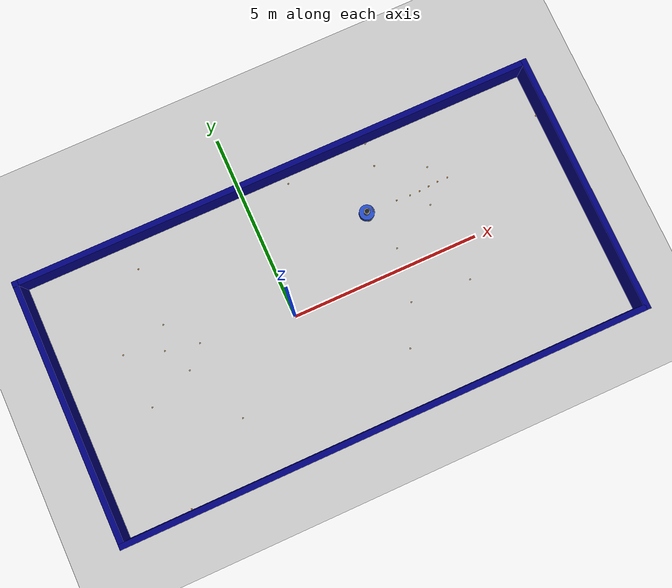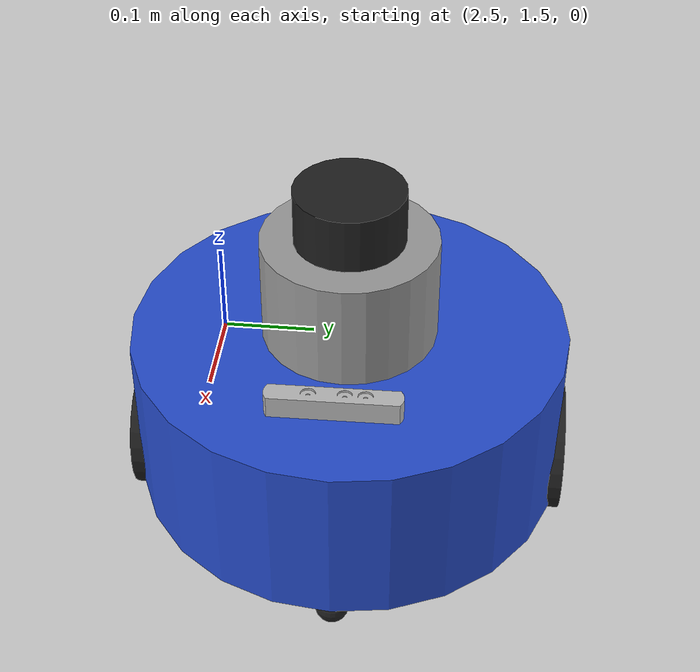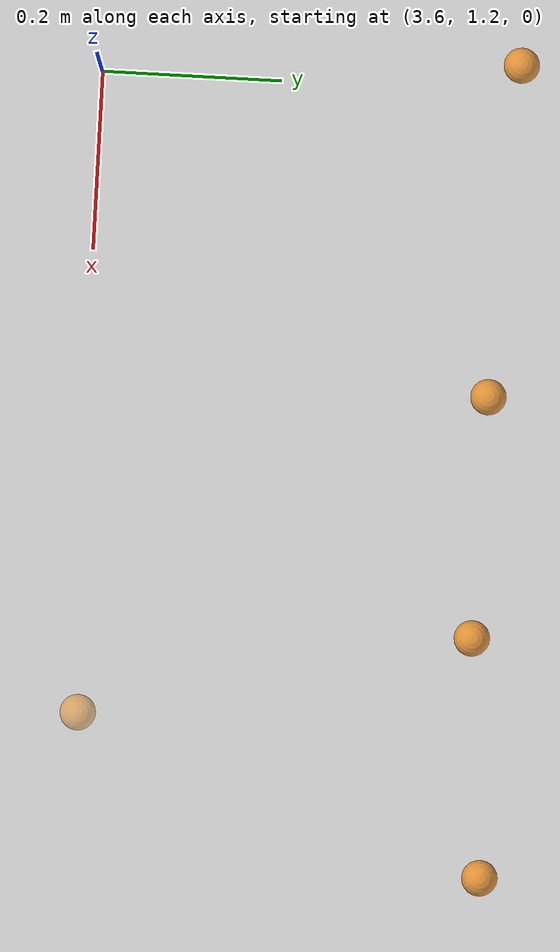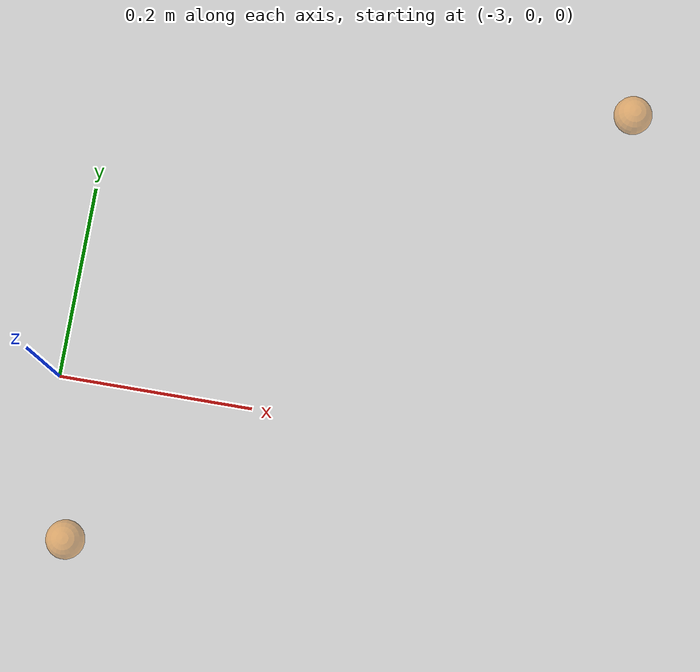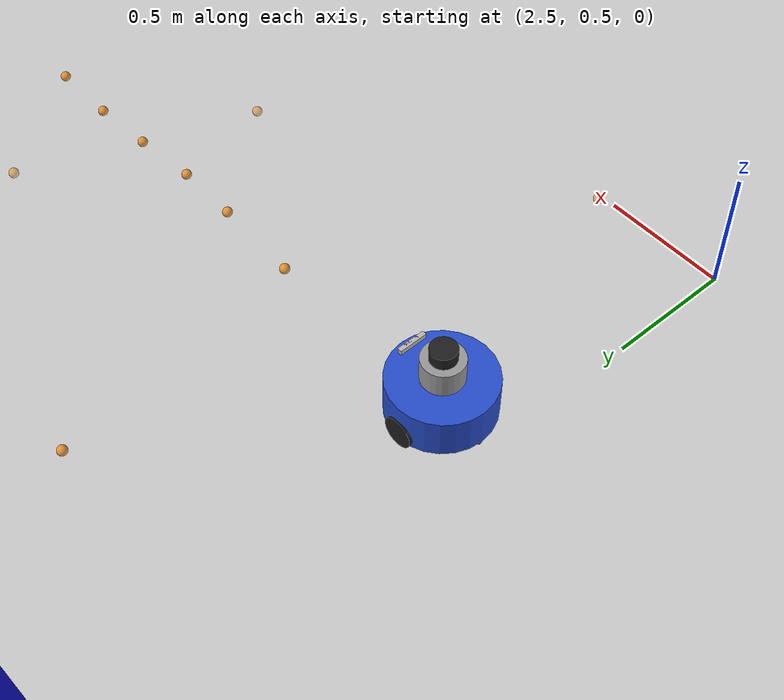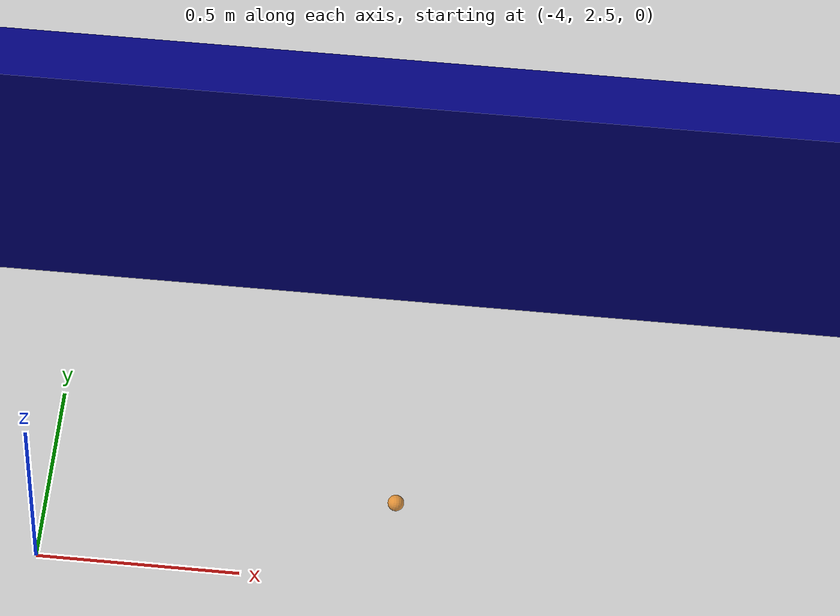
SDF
<sdf version="1.6">
 <world name="default">
  <model name="ground_plane">
   <static>1</static>
   <link name="link">
    <collision name="collision">
     <geometry><plane><normal>0 0 1</normal><size>100 100</size></plane></geometry>
     <surface><friction><ode><mu>100</mu><mu2>50</mu2></ode></friction></surface>
    </collision>
    <visual name="visual">
     <cast_shadows>0</cast_shadows>
     <geometry><plane><normal>0 0 1</normal><size>100 100</size></plane></geometry>
     <material>
      <script><uri>file://media/materials/scripts/gazebo.material</uri><name>Gazebo/Grey</name></script>
     </material>
    </visual>
   </link>
  </model>
  <gravity>0 0 -9.8</gravity>
  <magnetic_field>6e-06 2.3e-05 -4.2e-05</magnetic_field>
  <atmosphere type="adiabatic"/>
  <physics name="default_physics" default="0" type="ode">
   <max_step_size>0.001</max_step_size>
   <real_time_factor>1</real_time_factor>
   <real_time_update_rate>1000</real_time_update_rate>
  </physics>
  <scene><ambient>0.4 0.4 0.4 1</ambient><background>0.7 0.7 0.7 1</background><shadows>1</shadows></scene>
  <spherical_coordinates>
   <surface_model>EARTH_WGS84</surface_model>
   <latitude_deg>0</latitude_deg>
   <longitude_deg>0</longitude_deg>
   <elevation>0</elevation>
   <heading_deg>0</heading_deg>
  </spherical_coordinates>
  <model name="table_tennis_room_2">
   <pose>0.979802 0.03249 0 0 -0 0</pose>
   <link name="Wall_3">
    <collision name="Wall_3_Collision">
     <geometry><box><size>14 0.15 0.76</size></box></geometry>
     <pose>0 0 0.38 0 -0 0</pose>
    </collision>
    <visual name="Wall_3_Visual">
     <pose>0 0 0.38 0 -0 0</pose>
     <geometry><box><size>14 0.15 0.76</size></box></geometry>
     <material>
      <script><uri>file://media/materials/scripts/gazebo.material</uri><name>Gazebo/Grey</name></script>
      <ambient>0 0 0.498039 1</ambient>
     </material>
    </visual>
    <pose>0 -3.425 0 0 -0 0</pose>
   </link>
   <link name="Wall_4">
    <collision name="Wall_4_Collision">
     <geometry><box><size>7 0.15 0.76</size></box></geometry>
     <pose>0 0 0.38 0 -0 0</pose>
    </collision>
    <visual name="Wall_4_Visual">
     <pose>0 0 0.38 0 -0 0</pose>
     <geometry><box><size>7 0.15 0.76</size></box></geometry>
     <material>
      <script><uri>file://media/materials/scripts/gazebo.material</uri><name>Gazebo/Grey</name></script>
      <ambient>0 0 0.498039 1</ambient>
     </material>
    </visual>
    <pose>6.925 0 0 0 -0 1.5708</pose>
   </link>
   <link name="Wall_5">
    <collision name="Wall_5_Collision">
     <geometry><box><size>14 0.15 0.76</size></box></geometry>
     <pose>0 0 0.38 0 -0 0</pose>
    </collision>
    <visual name="Wall_5_Visual">
     <pose>0 0 0.38 0 -0 0</pose>
     <geometry><box><size>14 0.15 0.76</size></box></geometry>
     <material>
      <script><uri>file://media/materials/scripts/gazebo.material</uri><name>Gazebo/Grey</name></script>
      <ambient>0 0 0.498039 1</ambient>
     </material>
    </visual>
    <pose>0 3.425 0 0 -0 3.14159</pose>
   </link>
   <link name="Wall_6">
    <collision name="Wall_6_Collision">
     <geometry><box><size>7 0.15 0.76</size></box></geometry>
     <pose>0 0 0.38 0 -0 0</pose>
    </collision>
    <visual name="Wall_6_Visual">
     <pose>0 0 0.38 0 -0 0</pose>
     <geometry><box><size>7 0.15 0.76</size></box></geometry>
     <material>
      <script><uri>file://media/materials/scripts/gazebo.material</uri><name>Gazebo/Grey</name></script>
      <ambient>0 0 0.498039 1</ambient>
     </material>
    </visual>
    <pose>-6.925 0 0 0 0 -1.5708</pose>
   </link>
   <static>1</static>
  </model>
  <model name="table_tennis">
   <link name="link">
    <inertial>
     <mass>0.0027</mass>
     <inertia><ixx>0.1</ixx><ixy>0</ixy><ixz>0</ixz><iyy>0.1</iyy><iyz>0</iyz><izz>0.1</izz></inertia>
    </inertial>
    <visual name="visual">
     <geometry><sphere><radius>0.02</radius></sphere></geometry>
     <material>
      <script>
       <name>Gazebo/OrangeTransparent</name>
       <uri>file://media/materials/scripts/gazebo.material</uri>
      </script>
      <ambient>1 0.44 0 1</ambient>
      <diffuse>1 0.44 0 1</diffuse>
      <specular>0 0 0 1</specular>
      <emissive>0 0 0 1</emissive>
      <shader type="vertex"><normal_map>__default__</normal_map></shader>
     </material>
     <transparency>0.22</transparency>
    </visual>
    <collision name="collision">
     <geometry><sphere><radius>0.02</radius></sphere></geometry>
     <surface>
      <friction>
       <ode><mu>1</mu><mu2>1</mu2><fdir1>0 0 0</fdir1><slip1>0</slip1><slip2>0</slip2></ode>
       <torsional>
        <coefficient>1</coefficient>
        <patch_radius>0</patch_radius>
        <surface_radius>0</surface_radius>
        <use_patch_radius>1</use_patch_radius>
        <ode><slip>0</slip></ode>
       </torsional>
      </friction>
      <bounce><restitution_coefficient>0</restitution_coefficient><threshold>1e+06</threshold></bounce>
      <contact>
       <collide_without_contact>0</collide_without_contact>
       <collide_without_contact_bitmask>1</collide_without_contact_bitmask>
       <collide_bitmask>1</collide_bitmask>
       <ode>
        <soft_cfm>0</soft_cfm>
        <soft_erp>0.2</soft_erp>
        <kp>1e+13</kp>
        <kd>1</kd>
        <max_vel>0.01</max_vel>
        <min_depth>0</min_depth>
       </ode>
       <bullet>
        <split_impulse>1</split_impulse>
        <split_impulse_penetration_threshold>-0.01</split_impulse_penetration_threshold>
        <soft_cfm>0</soft_cfm>
        <soft_erp>0.2</soft_erp>
        <kp>1e+13</kp>
        <kd>1</kd>
       </bullet>
      </contact>
     </surface>
    </collision>
   </link>
   <static>0</static>
   <pose>-2.95954 -0.163296 0.02 0 -0 0</pose>
  </model>
  <model name="table_tennis_0">
   <link name="link">
    <inertial>
     <mass>0.0027</mass>
     <inertia><ixx>0.1</ixx><ixy>0</ixy><ixz>0</ixz><iyy>0.1</iyy><iyz>0</iyz><izz>0.1</izz></inertia>
    </inertial>
    <visual name="visual">
     <geometry><sphere><radius>0.02</radius></sphere></geometry>
     <material>
      <script>
       <name>Gazebo/OrangeTransparent</name>
       <uri>file://media/materials/scripts/gazebo.material</uri>
      </script>
      <ambient>1 0.44 0 1</ambient>
      <diffuse>1 0.44 0 1</diffuse>
      <specular>0 0 0 1</specular>
      <emissive>0 0 0 1</emissive>
      <shader type="vertex"><normal_map>__default__</normal_map></shader>
     </material>
     <transparency>0.22</transparency>
    </visual>
    <collision name="collision">
     <geometry><sphere><radius>0.02</radius></sphere></geometry>
     <surface>
      <friction>
       <ode><mu>1</mu><mu2>1</mu2><fdir1>0 0 0</fdir1><slip1>0</slip1><slip2>0</slip2></ode>
       <torsional>
        <coefficient>1</coefficient>
        <patch_radius>0</patch_radius>
        <surface_radius>0</surface_radius>
        <use_patch_radius>1</use_patch_radius>
        <ode><slip>0</slip></ode>
       </torsional>
      </friction>
      <bounce><restitution_coefficient>0</restitution_coefficient><threshold>1e+06</threshold></bounce>
      <contact>
       <collide_without_contact>0</collide_without_contact>
       <collide_without_contact_bitmask>1</collide_without_contact_bitmask>
       <collide_bitmask>1</collide_bitmask>
       <ode>
        <soft_cfm>0</soft_cfm>
        <soft_erp>0.2</soft_erp>
        <kp>1e+13</kp>
        <kd>1</kd>
        <max_vel>0.01</max_vel>
        <min_depth>0</min_depth>
       </ode>
       <bullet>
        <split_impulse>1</split_impulse>
        <split_impulse_penetration_threshold>-0.01</split_impulse_penetration_threshold>
        <soft_cfm>0</soft_cfm>
        <soft_erp>0.2</soft_erp>
        <kp>1e+13</kp>
        <kd>1</kd>
       </bullet>
      </contact>
     </surface>
    </collision>
   </link>
   <static>0</static>
   <pose>-4.32968 0.872251 0.02 0 -0 0</pose>
  </model>
  <model name="table_tennis_1">
   <link name="link">
    <inertial>
     <mass>0.0027</mass>
     <inertia><ixx>0.1</ixx><ixy>0</ixy><ixz>0</ixz><iyy>0.1</iyy><iyz>0</iyz><izz>0.1</izz></inertia>
    </inertial>
    <visual name="visual">
     <geometry><sphere><radius>0.02</radius></sphere></geometry>
     <material>
      <script>
       <name>Gazebo/OrangeTransparent</name>
       <uri>file://media/materials/scripts/gazebo.material</uri>
      </script>
      <ambient>1 0.44 0 1</ambient>
      <diffuse>1 0.44 0 1</diffuse>
      <specular>0 0 0 1</specular>
      <emissive>0 0 0 1</emissive>
      <shader type="vertex"><normal_map>__default__</normal_map></shader>
     </material>
     <transparency>0.22</transparency>
    </visual>
    <collision name="collision">
     <geometry><sphere><radius>0.02</radius></sphere></geometry>
     <surface>
      <friction>
       <ode><mu>1</mu><mu2>1</mu2><fdir1>0 0 0</fdir1><slip1>0</slip1><slip2>0</slip2></ode>
       <torsional>
        <coefficient>1</coefficient>
        <patch_radius>0</patch_radius>
        <surface_radius>0</surface_radius>
        <use_patch_radius>1</use_patch_radius>
        <ode><slip>0</slip></ode>
       </torsional>
      </friction>
      <bounce><restitution_coefficient>0</restitution_coefficient><threshold>1e+06</threshold></bounce>
      <contact>
       <collide_without_contact>0</collide_without_contact>
       <collide_without_contact_bitmask>1</collide_without_contact_bitmask>
       <collide_bitmask>1</collide_bitmask>
       <ode>
        <soft_cfm>0</soft_cfm>
        <soft_erp>0.2</soft_erp>
        <kp>1e+13</kp>
        <kd>1</kd>
        <max_vel>0.01</max_vel>
        <min_depth>0</min_depth>
       </ode>
       <bullet>
        <split_impulse>1</split_impulse>
        <split_impulse_penetration_threshold>-0.01</split_impulse_penetration_threshold>
        <soft_cfm>0</soft_cfm>
        <soft_erp>0.2</soft_erp>
        <kp>1e+13</kp>
        <kd>1</kd>
       </bullet>
      </contact>
     </surface>
    </collision>
   </link>
   <static>0</static>
   <pose>-3.34024 0.546321 0.02 0 -0 0</pose>
  </model>
  <model name="table_tennis_2">
   <link name="link">
    <inertial>
     <mass>0.0027</mass>
     <inertia><ixx>0.1</ixx><ixy>0</ixy><ixz>0</ixz><iyy>0.1</iyy><iyz>0</iyz><izz>0.1</izz></inertia>
    </inertial>
    <visual name="visual">
     <geometry><sphere><radius>0.02</radius></sphere></geometry>
     <material>
      <script>
       <name>Gazebo/OrangeTransparent</name>
       <uri>file://media/materials/scripts/gazebo.material</uri>
      </script>
      <ambient>1 0.44 0 1</ambient>
      <diffuse>1 0.44 0 1</diffuse>
      <specular>0 0 0 1</specular>
      <emissive>0 0 0 1</emissive>
      <shader type="vertex"><normal_map>__default__</normal_map></shader>
     </material>
     <transparency>0.22</transparency>
    </visual>
    <collision name="collision">
     <geometry><sphere><radius>0.02</radius></sphere></geometry>
     <surface>
      <friction>
       <ode><mu>1</mu><mu2>1</mu2><fdir1>0 0 0</fdir1><slip1>0</slip1><slip2>0</slip2></ode>
       <torsional>
        <coefficient>1</coefficient>
        <patch_radius>0</patch_radius>
        <surface_radius>0</surface_radius>
        <use_patch_radius>1</use_patch_radius>
        <ode><slip>0</slip></ode>
       </torsional>
      </friction>
      <bounce><restitution_coefficient>0</restitution_coefficient><threshold>1e+06</threshold></bounce>
      <contact>
       <collide_without_contact>0</collide_without_contact>
       <collide_without_contact_bitmask>1</collide_without_contact_bitmask>
       <collide_bitmask>1</collide_bitmask>
       <ode>
        <soft_cfm>0</soft_cfm>
        <soft_erp>0.2</soft_erp>
        <kp>1e+13</kp>
        <kd>1</kd>
        <max_vel>0.01</max_vel>
        <min_depth>0</min_depth>
       </ode>
       <bullet>
        <split_impulse>1</split_impulse>
        <split_impulse_penetration_threshold>-0.01</split_impulse_penetration_threshold>
        <soft_cfm>0</soft_cfm>
        <soft_erp>0.2</soft_erp>
        <kp>1e+13</kp>
        <kd>1</kd>
       </bullet>
      </contact>
     </surface>
    </collision>
   </link>
   <static>0</static>
   <pose>-4.16554 -0.61973 0.02 -5e-06 -1e-06 0</pose>
  </model>
  <model name="table_tennis_3">
   <link name="link">
    <inertial>
     <mass>0.0027</mass>
     <inertia><ixx>0.1</ixx><ixy>0</ixy><ixz>0</ixz><iyy>0.1</iyy><iyz>0</iyz><izz>0.1</izz></inertia>
    </inertial>
    <visual name="visual">
     <geometry><sphere><radius>0.02</radius></sphere></geometry>
     <material>
      <script>
       <name>Gazebo/OrangeTransparent</name>
       <uri>file://media/materials/scripts/gazebo.material</uri>
      </script>
      <ambient>1 0.44 0 1</ambient>
      <diffuse>1 0.44 0 1</diffuse>
      <specular>0 0 0 1</specular>
      <emissive>0 0 0 1</emissive>
      <shader type="vertex"><normal_map>__default__</normal_map></shader>
     </material>
     <transparency>0.22</transparency>
    </visual>
    <collision name="collision">
     <geometry><sphere><radius>0.02</radius></sphere></geometry>
     <surface>
      <friction>
       <ode><mu>1</mu><mu2>1</mu2><fdir1>0 0 0</fdir1><slip1>0</slip1><slip2>0</slip2></ode>
       <torsional>
        <coefficient>1</coefficient>
        <patch_radius>0</patch_radius>
        <surface_radius>0</surface_radius>
        <use_patch_radius>1</use_patch_radius>
        <ode><slip>0</slip></ode>
       </torsional>
      </friction>
      <bounce><restitution_coefficient>0</restitution_coefficient><threshold>1e+06</threshold></bounce>
      <contact>
       <collide_without_contact>0</collide_without_contact>
       <collide_without_contact_bitmask>1</collide_without_contact_bitmask>
       <collide_bitmask>1</collide_bitmask>
       <ode>
        <soft_cfm>0</soft_cfm>
        <soft_erp>0.2</soft_erp>
        <kp>1e+13</kp>
        <kd>1</kd>
        <max_vel>0.01</max_vel>
        <min_depth>0</min_depth>
       </ode>
       <bullet>
        <split_impulse>1</split_impulse>
        <split_impulse_penetration_threshold>-0.01</split_impulse_penetration_threshold>
        <soft_cfm>0</soft_cfm>
        <soft_erp>0.2</soft_erp>
        <kp>1e+13</kp>
        <kd>1</kd>
       </bullet>
      </contact>
     </surface>
    </collision>
   </link>
   <static>0</static>
   <pose>-2.21963 -1.78059 0.02 0 -0 0</pose>
  </model>
  <model name="table_tennis_4">
   <link name="link">
    <inertial>
     <mass>0.0027</mass>
     <inertia><ixx>0.1</ixx><ixy>0</ixy><ixz>0</ixz><iyy>0.1</iyy><iyz>0</iyz><izz>0.1</izz></inertia>
    </inertial>
    <visual name="visual">
     <geometry><sphere><radius>0.02</radius></sphere></geometry>
     <material>
      <script>
       <name>Gazebo/OrangeTransparent</name>
       <uri>file://media/materials/scripts/gazebo.material</uri>
      </script>
      <ambient>1 0.44 0 1</ambient>
      <diffuse>1 0.44 0 1</diffuse>
      <specular>0 0 0 1</specular>
      <emissive>0 0 0 1</emissive>
      <shader type="vertex"><normal_map>__default__</normal_map></shader>
     </material>
     <transparency>0.22</transparency>
    </visual>
    <collision name="collision">
     <geometry><sphere><radius>0.02</radius></sphere></geometry>
     <surface>
      <friction>
       <ode><mu>1</mu><mu2>1</mu2><fdir1>0 0 0</fdir1><slip1>0</slip1><slip2>0</slip2></ode>
       <torsional>
        <coefficient>1</coefficient>
        <patch_radius>0</patch_radius>
        <surface_radius>0</surface_radius>
        <use_patch_radius>1</use_patch_radius>
        <ode><slip>0</slip></ode>
       </torsional>
      </friction>
      <bounce><restitution_coefficient>0</restitution_coefficient><threshold>1e+06</threshold></bounce>
      <contact>
       <collide_without_contact>0</collide_without_contact>
       <collide_without_contact_bitmask>1</collide_without_contact_bitmask>
       <collide_bitmask>1</collide_bitmask>
       <ode>
        <soft_cfm>0</soft_cfm>
        <soft_erp>0.2</soft_erp>
        <kp>1e+13</kp>
        <kd>1</kd>
        <max_vel>0.01</max_vel>
        <min_depth>0</min_depth>
       </ode>
       <bullet>
        <split_impulse>1</split_impulse>
        <split_impulse_penetration_threshold>-0.01</split_impulse_penetration_threshold>
        <soft_cfm>0</soft_cfm>
        <soft_erp>0.2</soft_erp>
        <kp>1e+13</kp>
        <kd>1</kd>
       </bullet>
      </contact>
     </surface>
    </collision>
   </link>
   <static>0</static>
   <pose>-3.12084 1.17118 0.02 0 -0 0</pose>
  </model>
  <model name="table_tennis_5">
   <link name="link">
    <inertial>
     <mass>0.0027</mass>
     <inertia><ixx>0.1</ixx><ixy>0</ixy><ixz>0</ixz><iyy>0.1</iyy><iyz>0</iyz><izz>0.1</izz></inertia>
    </inertial>
    <visual name="visual">
     <geometry><sphere><radius>0.02</radius></sphere></geometry>
     <material>
      <script>
       <name>Gazebo/OrangeTransparent</name>
       <uri>file://media/materials/scripts/gazebo.material</uri>
      </script>
      <ambient>1 0.44 0 1</ambient>
      <diffuse>1 0.44 0 1</diffuse>
      <specular>0 0 0 1</specular>
      <emissive>0 0 0 1</emissive>
      <shader type="vertex"><normal_map>__default__</normal_map></shader>
     </material>
     <transparency>0.22</transparency>
    </visual>
    <collision name="collision">
     <geometry><sphere><radius>0.02</radius></sphere></geometry>
     <surface>
      <friction>
       <ode><mu>1</mu><mu2>1</mu2><fdir1>0 0 0</fdir1><slip1>0</slip1><slip2>0</slip2></ode>
       <torsional>
        <coefficient>1</coefficient>
        <patch_radius>0</patch_radius>
        <surface_radius>0</surface_radius>
        <use_patch_radius>1</use_patch_radius>
        <ode><slip>0</slip></ode>
       </torsional>
      </friction>
      <bounce><restitution_coefficient>0</restitution_coefficient><threshold>1e+06</threshold></bounce>
      <contact>
       <collide_without_contact>0</collide_without_contact>
       <collide_without_contact_bitmask>1</collide_without_contact_bitmask>
       <collide_bitmask>1</collide_bitmask>
       <ode>
        <soft_cfm>0</soft_cfm>
        <soft_erp>0.2</soft_erp>
        <kp>1e+13</kp>
        <kd>1</kd>
        <max_vel>0.01</max_vel>
        <min_depth>0</min_depth>
       </ode>
       <bullet>
        <split_impulse>1</split_impulse>
        <split_impulse_penetration_threshold>-0.01</split_impulse_penetration_threshold>
        <soft_cfm>0</soft_cfm>
        <soft_erp>0.2</soft_erp>
        <kp>1e+13</kp>
        <kd>1</kd>
       </bullet>
      </contact>
     </surface>
    </collision>
   </link>
   <static>0</static>
   <pose>-2.46176 0.366007 0.02 0 -0 0</pose>
  </model>
  <model name="table_tennis_6">
   <link name="link">
    <inertial>
     <mass>0.0027</mass>
     <inertia><ixx>0.1</ixx><ixy>0</ixy><ixz>0</ixz><iyy>0.1</iyy><iyz>0</iyz><izz>0.1</izz></inertia>
    </inertial>
    <visual name="visual">
     <geometry><sphere><radius>0.02</radius></sphere></geometry>
     <material>
      <script>
       <name>Gazebo/OrangeTransparent</name>
       <uri>file://media/materials/scripts/gazebo.material</uri>
      </script>
      <ambient>1 0.44 0 1</ambient>
      <diffuse>1 0.44 0 1</diffuse>
      <specular>0 0 0 1</specular>
      <emissive>0 0 0 1</emissive>
      <shader type="vertex"><normal_map>__default__</normal_map></shader>
     </material>
     <transparency>0.22</transparency>
    </visual>
    <collision name="collision">
     <geometry><sphere><radius>0.02</radius></sphere></geometry>
     <surface>
      <friction>
       <ode><mu>1</mu><mu2>1</mu2><fdir1>0 0 0</fdir1><slip1>0</slip1><slip2>0</slip2></ode>
       <torsional>
        <coefficient>1</coefficient>
        <patch_radius>0</patch_radius>
        <surface_radius>0</surface_radius>
        <use_patch_radius>1</use_patch_radius>
        <ode><slip>0</slip></ode>
       </torsional>
      </friction>
      <bounce><restitution_coefficient>0</restitution_coefficient><threshold>1e+06</threshold></bounce>
      <contact>
       <collide_without_contact>0</collide_without_contact>
       <collide_without_contact_bitmask>1</collide_without_contact_bitmask>
       <collide_bitmask>1</collide_bitmask>
       <ode>
        <soft_cfm>0</soft_cfm>
        <soft_erp>0.2</soft_erp>
        <kp>1e+13</kp>
        <kd>1</kd>
        <max_vel>0.01</max_vel>
        <min_depth>0</min_depth>
       </ode>
       <bullet>
        <split_impulse>1</split_impulse>
        <split_impulse_penetration_threshold>-0.01</split_impulse_penetration_threshold>
        <soft_cfm>0</soft_cfm>
        <soft_erp>0.2</soft_erp>
        <kp>1e+13</kp>
        <kd>1</kd>
       </bullet>
      </contact>
     </surface>
    </collision>
   </link>
   <static>0</static>
   <pose>2.8061 -0.868332 0.02 0 -0 0</pose>
  </model>
  <model name="table_tennis_7">
   <link name="link">
    <inertial>
     <mass>0.0027</mass>
     <inertia><ixx>0.1</ixx><ixy>0</ixy><ixz>0</ixz><iyy>0.1</iyy><iyz>0</iyz><izz>0.1</izz></inertia>
    </inertial>
    <visual name="visual">
     <geometry><sphere><radius>0.02</radius></sphere></geometry>
     <material>
      <script>
       <name>Gazebo/OrangeTransparent</name>
       <uri>file://media/materials/scripts/gazebo.material</uri>
      </script>
      <ambient>1 0.44 0 1</ambient>
      <diffuse>1 0.44 0 1</diffuse>
      <specular>0 0 0 1</specular>
      <emissive>0 0 0 1</emissive>
      <shader type="vertex"><normal_map>__default__</normal_map></shader>
     </material>
     <transparency>0.22</transparency>
    </visual>
    <collision name="collision">
     <geometry><sphere><radius>0.02</radius></sphere></geometry>
     <surface>
      <friction>
       <ode><mu>1</mu><mu2>1</mu2><fdir1>0 0 0</fdir1><slip1>0</slip1><slip2>0</slip2></ode>
       <torsional>
        <coefficient>1</coefficient>
        <patch_radius>0</patch_radius>
        <surface_radius>0</surface_radius>
        <use_patch_radius>1</use_patch_radius>
        <ode><slip>0</slip></ode>
       </torsional>
      </friction>
      <bounce><restitution_coefficient>0</restitution_coefficient><threshold>1e+06</threshold></bounce>
      <contact>
       <collide_without_contact>0</collide_without_contact>
       <collide_without_contact_bitmask>1</collide_without_contact_bitmask>
       <collide_bitmask>1</collide_bitmask>
       <ode>
        <soft_cfm>0</soft_cfm>
        <soft_erp>0.2</soft_erp>
        <kp>1e+13</kp>
        <kd>1</kd>
        <max_vel>0.01</max_vel>
        <min_depth>0</min_depth>
       </ode>
       <bullet>
        <split_impulse>1</split_impulse>
        <split_impulse_penetration_threshold>-0.01</split_impulse_penetration_threshold>
        <soft_cfm>0</soft_cfm>
        <soft_erp>0.2</soft_erp>
        <kp>1e+13</kp>
        <kd>1</kd>
       </bullet>
      </contact>
     </surface>
    </collision>
   </link>
   <static>0</static>
   <pose>2.28577 -1.92107 0.02 0 -0 0</pose>
  </model>
  <model name="table_tennis_8">
   <link name="link">
    <inertial>
     <mass>0.0027</mass>
     <inertia><ixx>0.1</ixx><ixy>0</ixy><ixz>0</ixz><iyy>0.1</iyy><iyz>0</iyz><izz>0.1</izz></inertia>
    </inertial>
    <visual name="visual">
     <geometry><sphere><radius>0.02</radius></sphere></geometry>
     <material>
      <script>
       <name>Gazebo/OrangeTransparent</name>
       <uri>file://media/materials/scripts/gazebo.material</uri>
      </script>
      <ambient>1 0.44 0 1</ambient>
      <diffuse>1 0.44 0 1</diffuse>
      <specular>0 0 0 1</specular>
      <emissive>0 0 0 1</emissive>
      <shader type="vertex"><normal_map>__default__</normal_map></shader>
     </material>
     <transparency>0.22</transparency>
    </visual>
    <collision name="collision">
     <geometry><sphere><radius>0.02</radius></sphere></geometry>
     <surface>
      <friction>
       <ode><mu>1</mu><mu2>1</mu2><fdir1>0 0 0</fdir1><slip1>0</slip1><slip2>0</slip2></ode>
       <torsional>
        <coefficient>1</coefficient>
        <patch_radius>0</patch_radius>
        <surface_radius>0</surface_radius>
        <use_patch_radius>1</use_patch_radius>
        <ode><slip>0</slip></ode>
       </torsional>
      </friction>
      <bounce><restitution_coefficient>0</restitution_coefficient><threshold>1e+06</threshold></bounce>
      <contact>
       <collide_without_contact>0</collide_without_contact>
       <collide_without_contact_bitmask>1</collide_without_contact_bitmask>
       <collide_bitmask>1</collide_bitmask>
       <ode>
        <soft_cfm>0</soft_cfm>
        <soft_erp>0.2</soft_erp>
        <kp>1e+13</kp>
        <kd>1</kd>
        <max_vel>0.01</max_vel>
        <min_depth>0</min_depth>
       </ode>
       <bullet>
        <split_impulse>1</split_impulse>
        <split_impulse_penetration_threshold>-0.01</split_impulse_penetration_threshold>
        <soft_cfm>0</soft_cfm>
        <soft_erp>0.2</soft_erp>
        <kp>1e+13</kp>
        <kd>1</kd>
       </bullet>
      </contact>
     </surface>
    </collision>
   </link>
   <static>0</static>
   <pose>3.05775 0.533081 0.02 0 -0 0</pose>
  </model>
  <model name="table_tennis_9">
   <link name="link">
    <inertial>
     <mass>0.0027</mass>
     <inertia><ixx>0.1</ixx><ixy>0</ixy><ixz>0</ixz><iyy>0.1</iyy><iyz>0</iyz><izz>0.1</izz></inertia>
    </inertial>
    <visual name="visual">
     <geometry><sphere><radius>0.02</radius></sphere></geometry>
     <material>
      <script>
       <name>Gazebo/OrangeTransparent</name>
       <uri>file://media/materials/scripts/gazebo.material</uri>
      </script>
      <ambient>1 0.44 0 1</ambient>
      <diffuse>1 0.44 0 1</diffuse>
      <specular>0 0 0 1</specular>
      <emissive>0 0 0 1</emissive>
      <shader type="vertex"><normal_map>__default__</normal_map></shader>
     </material>
     <transparency>0.22</transparency>
    </visual>
    <collision name="collision">
     <geometry><sphere><radius>0.02</radius></sphere></geometry>
     <surface>
      <friction>
       <ode><mu>1</mu><mu2>1</mu2><fdir1>0 0 0</fdir1><slip1>0</slip1><slip2>0</slip2></ode>
       <torsional>
        <coefficient>1</coefficient>
        <patch_radius>0</patch_radius>
        <surface_radius>0</surface_radius>
        <use_patch_radius>1</use_patch_radius>
        <ode><slip>0</slip></ode>
       </torsional>
      </friction>
      <bounce><restitution_coefficient>0</restitution_coefficient><threshold>1e+06</threshold></bounce>
      <contact>
       <collide_without_contact>0</collide_without_contact>
       <collide_without_contact_bitmask>1</collide_without_contact_bitmask>
       <collide_bitmask>1</collide_bitmask>
       <ode>
        <soft_cfm>0</soft_cfm>
        <soft_erp>0.2</soft_erp>
        <kp>1e+13</kp>
        <kd>1</kd>
        <max_vel>0.01</max_vel>
        <min_depth>0</min_depth>
       </ode>
       <bullet>
        <split_impulse>1</split_impulse>
        <split_impulse_penetration_threshold>-0.01</split_impulse_penetration_threshold>
        <soft_cfm>0</soft_cfm>
        <soft_erp>0.2</soft_erp>
        <kp>1e+13</kp>
        <kd>1</kd>
       </bullet>
      </contact>
     </surface>
    </collision>
   </link>
   <static>0</static>
   <pose>3.45914 3.36247 0.020008 -2.40865 0.565541 -0.486457</pose>
  </model>
  <model name="table_tennis_10">
   <link name="link">
    <inertial>
     <mass>0.0027</mass>
     <inertia><ixx>0.1</ixx><ixy>0</ixy><ixz>0</ixz><iyy>0.1</iyy><iyz>0</iyz><izz>0.1</izz></inertia>
    </inertial>
    <visual name="visual">
     <geometry><sphere><radius>0.02</radius></sphere></geometry>
     <material>
      <script>
       <name>Gazebo/OrangeTransparent</name>
       <uri>file://media/materials/scripts/gazebo.material</uri>
      </script>
      <ambient>1 0.44 0 1</ambient>
      <diffuse>1 0.44 0 1</diffuse>
      <specular>0 0 0 1</specular>
      <emissive>0 0 0 1</emissive>
      <shader type="vertex"><normal_map>__default__</normal_map></shader>
     </material>
     <transparency>0.22</transparency>
    </visual>
    <collision name="collision">
     <geometry><sphere><radius>0.02</radius></sphere></geometry>
     <surface>
      <friction>
       <ode><mu>1</mu><mu2>1</mu2><fdir1>0 0 0</fdir1><slip1>0</slip1><slip2>0</slip2></ode>
       <torsional>
        <coefficient>1</coefficient>
        <patch_radius>0</patch_radius>
        <surface_radius>0</surface_radius>
        <use_patch_radius>1</use_patch_radius>
        <ode><slip>0</slip></ode>
       </torsional>
      </friction>
      <bounce><restitution_coefficient>0</restitution_coefficient><threshold>1e+06</threshold></bounce>
      <contact>
       <collide_without_contact>0</collide_without_contact>
       <collide_without_contact_bitmask>1</collide_without_contact_bitmask>
       <collide_bitmask>1</collide_bitmask>
       <ode>
        <soft_cfm>0</soft_cfm>
        <soft_erp>0.2</soft_erp>
        <kp>1e+13</kp>
        <kd>1</kd>
        <max_vel>0.01</max_vel>
        <min_depth>0</min_depth>
       </ode>
       <bullet>
        <split_impulse>1</split_impulse>
        <split_impulse_penetration_threshold>-0.01</split_impulse_penetration_threshold>
        <soft_cfm>0</soft_cfm>
        <soft_erp>0.2</soft_erp>
        <kp>1e+13</kp>
        <kd>1</kd>
       </bullet>
      </contact>
     </surface>
    </collision>
   </link>
   <static>0</static>
   <pose>4.40709 -0.954895 0.02 0 -0 0</pose>
  </model>
  <model name="table_tennis_11">
   <link name="link">
    <inertial>
     <mass>0.0027</mass>
     <inertia><ixx>0.1</ixx><ixy>0</ixy><ixz>0</ixz><iyy>0.1</iyy><iyz>0</iyz><izz>0.1</izz></inertia>
    </inertial>
    <visual name="visual">
     <geometry><sphere><radius>0.02</radius></sphere></geometry>
     <material>
      <script>
       <name>Gazebo/OrangeTransparent</name>
       <uri>file://media/materials/scripts/gazebo.material</uri>
      </script>
      <ambient>1 0.44 0 1</ambient>
      <diffuse>1 0.44 0 1</diffuse>
      <specular>0 0 0 1</specular>
      <emissive>0 0 0 1</emissive>
      <shader type="vertex"><normal_map>__default__</normal_map></shader>
     </material>
     <transparency>0.22</transparency>
    </visual>
    <collision name="collision">
     <geometry><sphere><radius>0.02</radius></sphere></geometry>
     <surface>
      <friction>
       <ode><mu>1</mu><mu2>1</mu2><fdir1>0 0 0</fdir1><slip1>0</slip1><slip2>0</slip2></ode>
       <torsional>
        <coefficient>1</coefficient>
        <patch_radius>0</patch_radius>
        <surface_radius>0</surface_radius>
        <use_patch_radius>1</use_patch_radius>
        <ode><slip>0</slip></ode>
       </torsional>
      </friction>
      <bounce><restitution_coefficient>0</restitution_coefficient><threshold>1e+06</threshold></bounce>
      <contact>
       <collide_without_contact>0</collide_without_contact>
       <collide_without_contact_bitmask>1</collide_without_contact_bitmask>
       <collide_bitmask>1</collide_bitmask>
       <ode>
        <soft_cfm>0</soft_cfm>
        <soft_erp>0.2</soft_erp>
        <kp>1e+13</kp>
        <kd>1</kd>
        <max_vel>0.01</max_vel>
        <min_depth>0</min_depth>
       </ode>
       <bullet>
        <split_impulse>1</split_impulse>
        <split_impulse_penetration_threshold>-0.01</split_impulse_penetration_threshold>
        <soft_cfm>0</soft_cfm>
        <soft_erp>0.2</soft_erp>
        <kp>1e+13</kp>
        <kd>1</kd>
       </bullet>
      </contact>
     </surface>
    </collision>
   </link>
   <static>0</static>
   <pose>4.31509 1.21174 0.02 0 -0 0</pose>
  </model>
  <model name="table_tennis_12">
   <link name="link">
    <inertial>
     <mass>0.0027</mass>
     <inertia><ixx>0.1</ixx><ixy>0</ixy><ixz>0</ixz><iyy>0.1</iyy><iyz>0</iyz><izz>0.1</izz></inertia>
    </inertial>
    <visual name="visual">
     <geometry><sphere><radius>0.02</radius></sphere></geometry>
     <material>
      <script>
       <name>Gazebo/OrangeTransparent</name>
       <uri>file://media/materials/scripts/gazebo.material</uri>
      </script>
      <ambient>1 0.44 0 1</ambient>
      <diffuse>1 0.44 0 1</diffuse>
      <specular>0 0 0 1</specular>
      <emissive>0 0 0 1</emissive>
      <shader type="vertex"><normal_map>__default__</normal_map></shader>
     </material>
     <transparency>0.22</transparency>
    </visual>
    <collision name="collision">
     <geometry><sphere><radius>0.02</radius></sphere></geometry>
     <surface>
      <friction>
       <ode><mu>1</mu><mu2>1</mu2><fdir1>0 0 0</fdir1><slip1>0</slip1><slip2>0</slip2></ode>
       <torsional>
        <coefficient>1</coefficient>
        <patch_radius>0</patch_radius>
        <surface_radius>0</surface_radius>
        <use_patch_radius>1</use_patch_radius>
        <ode><slip>0</slip></ode>
       </torsional>
      </friction>
      <bounce><restitution_coefficient>0</restitution_coefficient><threshold>1e+06</threshold></bounce>
      <contact>
       <collide_without_contact>0</collide_without_contact>
       <collide_without_contact_bitmask>1</collide_without_contact_bitmask>
       <collide_bitmask>1</collide_bitmask>
       <ode>
        <soft_cfm>0</soft_cfm>
        <soft_erp>0.2</soft_erp>
        <kp>1e+13</kp>
        <kd>1</kd>
        <max_vel>0.01</max_vel>
        <min_depth>0</min_depth>
       </ode>
       <bullet>
        <split_impulse>1</split_impulse>
        <split_impulse_penetration_threshold>-0.01</split_impulse_penetration_threshold>
        <soft_cfm>0</soft_cfm>
        <soft_erp>0.2</soft_erp>
        <kp>1e+13</kp>
        <kd>1</kd>
       </bullet>
      </contact>
     </surface>
    </collision>
   </link>
   <static>0</static>
   <pose>4.66282 2.14576 0.02 0 -0 0</pose>
  </model>
  <model name="mbot">
   <link name="base_footprint">
    <inertial>
     <pose>0 0 0.136713 0 -0 0</pose>
     <mass>25.1</mass>
     <inertia><ixx>0.335625</ixx><ixy>0</ixy><ixz>0</ixz><iyy>0.335625</iyy><iyz>0</iyz><izz>0.426</izz></inertia>
    </inertial>
    <collision name="base_footprint_fixed_joint_lump__base_link_collision">
     <pose>0 0 0.11 0 -0 0</pose>
     <geometry><cylinder><length>0.16</length><radius>0.2</radius></cylinder></geometry>
    </collision>
    <collision name="base_footprint_fixed_joint_lump__kinect_link_collision_1">
     <pose>0.15 0 0.22 0 -0 0</pose>
     <geometry><box><size>0.07 0.3 0.09</size></box></geometry>
    </collision>
    <collision name="base_footprint_fixed_joint_lump__top_stage_link_collision_2">
     <pose>0 0 0.24 0 -0 0</pose>
     <geometry><cylinder><length>0.1</length><radius>0.08</radius></cylinder></geometry>
    </collision>
    <collision name="base_footprint_fixed_joint_lump__laser_link_collision_3">
     <pose>0 0 0.315 0 -0 0</pose>
     <geometry><cylinder><length>0.06</length><radius>0.05</radius></cylinder></geometry>
    </collision>
    <visual name="base_footprint_visual">
     <geometry><box><size>0.001 0.001 0.001</size></box></geometry>
     <material><script><uri>__default__</uri><name>__default__</name></script></material>
    </visual>
    <visual name="base_footprint_fixed_joint_lump__base_link_visual_1">
     <pose>0 0 0.11 0 -0 0</pose>
     <geometry><cylinder><length>0.16</length><radius>0.2</radius></cylinder></geometry>
     <material>
      <script><name>Gazebo/Blue</name><uri>file://media/materials/scripts/gazebo.material</uri></script>
     </material>
    </visual>
    <visual name="base_footprint_fixed_joint_lump__kinect_link_visual_2">
     <pose>0.15 0 0.22 0 -0 1.5708</pose>
     <geometry>
      <mesh><scale>1 1 1</scale><uri>/home/hyh/mc_ws/src/mbot_description_gazebo/meshes/kinect.dae</uri></mesh>
     </geometry>
     <material><script><uri>__default__</uri><name>__default__</name></script></material>
    </visual>
    <visual name="base_footprint_fixed_joint_lump__top_stage_link_visual_3">
     <pose>0 0 0.24 0 -0 0</pose>
     <geometry><cylinder><length>0.1</length><radius>0.08</radius></cylinder></geometry>
     <material>
      <script><name>Gazebo/Grey</name><uri>file://media/materials/scripts/gazebo.material</uri></script>
     </material>
    </visual>
    <visual name="base_footprint_fixed_joint_lump__laser_link_visual_4">
     <pose>0 0 0.315 0 -0 0</pose>
     <geometry><cylinder><length>0.05</length><radius>0.05</radius></cylinder></geometry>
     <material>
      <script><name>Gazebo/Black</name><uri>file://media/materials/scripts/gazebo.material</uri></script>
     </material>
    </visual>
    <sensor name="kinect" type="depth">
     <always_on>1</always_on>
     <update_rate>20</update_rate>
     <camera name="__default__">
      <horizontal_fov>1.0472</horizontal_fov>
      <image><format>R8G8B8</format><width>640</width><height>480</height></image>
      <clip><near>0.05</near><far>8</far></clip>
     </camera>
     <plugin name="kinect_kinect_controller" filename="libgazebo_ros_openni_kinect.so">
      <cameraName>kinect</cameraName>
      <alwaysOn>true</alwaysOn>
      <updateRate>10</updateRate>
      <imageTopicName>rgb/image_raw</imageTopicName>
      <depthImageTopicName>depth/image_raw</depthImageTopicName>
      <pointCloudTopicName>depth/points</pointCloudTopicName>
      <cameraInfoTopicName>rgb/camera_info</cameraInfoTopicName>
      <depthImageCameraInfoTopicName>depth/camera_info</depthImageCameraInfoTopicName>
      <frameName>kinect_frame_optical</frameName>
      <baseline>0.1</baseline>
      <distortion_k1>0.0</distortion_k1>
      <distortion_k2>0.0</distortion_k2>
      <distortion_k3>0.0</distortion_k3>
      <distortion_t1>0.0</distortion_t1>
      <distortion_t2>0.0</distortion_t2>
      <pointCloudCutoff>0.4</pointCloudCutoff>
      <robotNamespace>/mbot/</robotNamespace>
     </plugin>
     <pose>0.15 0 0.22 0 -0 0</pose>
    </sensor>
    <sensor name="rplidar" type="ray">
     <visualize>0</visualize>
     <update_rate>5.5</update_rate>
     <ray>
      <scan>
       <horizontal>
        <samples>360</samples>
        <resolution>1</resolution>
        <min_angle>-3</min_angle>
        <max_angle>3</max_angle>
       </horizontal>
       <vertical><samples>1</samples><min_angle>0</min_angle><max_angle>0</max_angle></vertical>
      </scan>
      <range><min>0.1</min><max>6</max><resolution>0.01</resolution></range>
      <noise><type>gaussian</type><mean>0</mean><stddev>0.01</stddev></noise>
     </ray>
     <plugin name="gazebo_rplidar" filename="libgazebo_ros_laser.so">
      <topicName>/scan</topicName>
      <frameName>laser_link</frameName>
      <robotNamespace>/mbot/</robotNamespace>
     </plugin>
     <pose>0 0 0.315 0 -0 0</pose>
    </sensor>
   </link>
   <link name="back_caster_link">
    <pose>0.18 0 0.015 0 -0 0</pose>
    <inertial>
     <mass>0.5</mass>
     <inertia><ixx>4.5e-05</ixx><ixy>0</ixy><ixz>0</ixz><iyy>4.5e-05</iyy><iyz>0</iyz><izz>4.5e-05</izz></inertia>
    </inertial>
    <collision name="back_caster_link_collision">
     <geometry><sphere><radius>0.015</radius></sphere></geometry>
    </collision>
    <visual name="back_caster_link_visual">
     <geometry><sphere><radius>0.015</radius></sphere></geometry>
     <material>
      <script><name>Gazebo/Black</name><uri>file://media/materials/scripts/gazebo.material</uri></script>
     </material>
    </visual>
   </link>
   <joint name="back_caster_joint" type="revolute">
    <child>back_caster_link</child>
    <parent>base_footprint</parent>
    <axis>
     <xyz>0 1 0</xyz>
     <limit><lower>-1e+16</lower><upper>1e+16</upper></limit>
     <dynamics><spring_reference>0</spring_reference><spring_stiffness>0</spring_stiffness></dynamics>
     <use_parent_model_frame>1</use_parent_model_frame>
    </axis>
   </joint>
   <link name="front_caster_link">
    <pose>-0.18 0 0.015 0 -0 0</pose>
    <inertial>
     <mass>0.5</mass>
     <inertia><ixx>4.5e-05</ixx><ixy>0</ixy><ixz>0</ixz><iyy>4.5e-05</iyy><iyz>0</iyz><izz>4.5e-05</izz></inertia>
    </inertial>
    <collision name="front_caster_link_collision">
     <geometry><sphere><radius>0.015</radius></sphere></geometry>
    </collision>
    <visual name="front_caster_link_visual">
     <geometry><sphere><radius>0.015</radius></sphere></geometry>
     <material>
      <script><name>Gazebo/Black</name><uri>file://media/materials/scripts/gazebo.material</uri></script>
     </material>
    </visual>
   </link>
   <joint name="front_caster_joint" type="revolute">
    <child>front_caster_link</child>
    <parent>base_footprint</parent>
    <axis>
     <xyz>0 1 0</xyz>
     <limit><lower>-1e+16</lower><upper>1e+16</upper></limit>
     <dynamics><spring_reference>0</spring_reference><spring_stiffness>0</spring_stiffness></dynamics>
     <use_parent_model_frame>1</use_parent_model_frame>
    </axis>
   </joint>
   <link name="left_wheel_link">
    <pose>0 -0.19 0.06 0 -0 0</pose>
    <inertial>
     <mass>2</mass>
     <inertia>
      <ixx>0.00190417</ixx>
      <ixy>0</ixy>
      <ixz>0</ixz>
      <iyy>0.00190417</iyy>
      <iyz>0</iyz>
      <izz>0.0036</izz>
     </inertia>
    </inertial>
    <collision name="left_wheel_link_collision">
     <pose>0 0 0 1.5708 -0 0</pose>
     <geometry><cylinder><length>0.025</length><radius>0.06</radius></cylinder></geometry>
    </collision>
    <visual name="left_wheel_link_visual">
     <pose>0 0 0 1.5708 -0 0</pose>
     <geometry><cylinder><length>0.025</length><radius>0.06</radius></cylinder></geometry>
     <material>
      <script><name>Gazebo/Black</name><uri>file://media/materials/scripts/gazebo.material</uri></script>
     </material>
    </visual>
   </link>
   <joint name="left_wheel_joint" type="revolute">
    <child>left_wheel_link</child>
    <parent>base_footprint</parent>
    <axis>
     <xyz>0 1 0</xyz>
     <limit><lower>-1e+16</lower><upper>1e+16</upper></limit>
     <dynamics><spring_reference>0</spring_reference><spring_stiffness>0</spring_stiffness></dynamics>
     <use_parent_model_frame>1</use_parent_model_frame>
    </axis>
   </joint>
   <link name="right_wheel_link">
    <pose>0 0.19 0.06 0 -0 0</pose>
    <inertial>
     <mass>2</mass>
     <inertia>
      <ixx>0.00190417</ixx>
      <ixy>0</ixy>
      <ixz>0</ixz>
      <iyy>0.00190417</iyy>
      <iyz>0</iyz>
      <izz>0.0036</izz>
     </inertia>
    </inertial>
    <collision name="right_wheel_link_collision">
     <pose>0 0 0 1.5708 -0 0</pose>
     <geometry><cylinder><length>0.025</length><radius>0.06</radius></cylinder></geometry>
    </collision>
    <visual name="right_wheel_link_visual">
     <pose>0 0 0 1.5708 -0 0</pose>
     <geometry><cylinder><length>0.025</length><radius>0.06</radius></cylinder></geometry>
     <material>
      <script><name>Gazebo/Black</name><uri>file://media/materials/scripts/gazebo.material</uri></script>
     </material>
    </visual>
   </link>
   <joint name="right_wheel_joint" type="revolute">
    <child>right_wheel_link</child>
    <parent>base_footprint</parent>
    <axis>
     <xyz>0 1 0</xyz>
     <limit><lower>-1e+16</lower><upper>1e+16</upper></limit>
     <dynamics><spring_reference>0</spring_reference><spring_stiffness>0</spring_stiffness></dynamics>
     <use_parent_model_frame>1</use_parent_model_frame>
    </axis>
   </joint>
   <static>0</static>
   <plugin name="gazebo_ros_control" filename="libgazebo_ros_control.so">
    <robotNamespace>/mbot</robotNamespace>
    <robotSimType>gazebo_ros_control/DefaultRobotHWSim</robotSimType>
    <legacyModeNS>true</legacyModeNS>
   </plugin>
   <pose>2.72524 1.66311 0 -0 -2e-06 0.012443</pose>
  </model>
  <model name="table_tennis_13">
   <link name="link">
    <pose>0 0 0.02 0 -0 0</pose>
    <inertial>
     <mass>0.0027</mass>
     <inertia><ixx>0.00027</ixx><ixy>0</ixy><ixz>0</ixz><iyy>0.00027</iyy><iyz>0</iyz><izz>0.00027</izz></inertia>
    </inertial>
    <visual name="visual">
     <geometry><sphere><radius>0.02</radius></sphere></geometry>
     <material>
      <script><name>Gazebo/Orange</name><uri>file://media/materials/scripts/gazebo.material</uri></script>
      <shader type="vertex"><normal_map>__default__</normal_map></shader>
     </material>
     <cast_shadows>0</cast_shadows>
     <transparency>0.22</transparency>
    </visual>
    <collision name="collision">
     <geometry><sphere><radius>0.02</radius></sphere></geometry>
     <surface>
      <friction>
       <ode><mu>1</mu><mu2>1</mu2><fdir1>0 0 0</fdir1><slip1>0</slip1><slip2>0</slip2></ode>
       <torsional>
        <coefficient>1</coefficient>
        <patch_radius>0</patch_radius>
        <surface_radius>0</surface_radius>
        <use_patch_radius>1</use_patch_radius>
        <ode><slip>0</slip></ode>
       </torsional>
      </friction>
      <bounce><restitution_coefficient>0</restitution_coefficient><threshold>1e+06</threshold></bounce>
      <contact>
       <collide_without_contact>0</collide_without_contact>
       <collide_without_contact_bitmask>1</collide_without_contact_bitmask>
       <collide_bitmask>1</collide_bitmask>
       <ode>
        <soft_cfm>0</soft_cfm>
        <soft_erp>0.2</soft_erp>
        <kp>1e+13</kp>
        <kd>1</kd>
        <max_vel>0.01</max_vel>
        <min_depth>0</min_depth>
       </ode>
       <bullet>
        <split_impulse>1</split_impulse>
        <split_impulse_penetration_threshold>-0.01</split_impulse_penetration_threshold>
        <soft_cfm>0</soft_cfm>
        <soft_erp>0.2</soft_erp>
        <kp>1e+13</kp>
        <kd>1</kd>
       </bullet>
      </contact>
     </surface>
    </collision>
   </link>
   <static>0</static>
   <pose>1.2021 3.20529 0.023495 1.79614 -0.672846 1.43621</pose>
  </model>
  <model name="table_tennis_14">
   <link name="link">
    <pose>0 0 0.02 0 -0 0</pose>
    <inertial>
     <mass>0.0027</mass>
     <inertia><ixx>0.00027</ixx><ixy>0</ixy><ixz>0</ixz><iyy>0.00027</iyy><iyz>0</iyz><izz>0.00027</izz></inertia>
    </inertial>
    <visual name="visual">
     <geometry><sphere><radius>0.02</radius></sphere></geometry>
     <material>
      <script><name>Gazebo/Orange</name><uri>file://media/materials/scripts/gazebo.material</uri></script>
      <shader type="vertex"><normal_map>__default__</normal_map></shader>
     </material>
     <cast_shadows>0</cast_shadows>
     <transparency>0.22</transparency>
    </visual>
    <collision name="collision">
     <geometry><sphere><radius>0.02</radius></sphere></geometry>
     <surface>
      <friction>
       <ode><mu>1</mu><mu2>1</mu2><fdir1>0 0 0</fdir1><slip1>0</slip1><slip2>0</slip2></ode>
       <torsional>
        <coefficient>1</coefficient>
        <patch_radius>0</patch_radius>
        <surface_radius>0</surface_radius>
        <use_patch_radius>1</use_patch_radius>
        <ode><slip>0</slip></ode>
       </torsional>
      </friction>
      <bounce><restitution_coefficient>0</restitution_coefficient><threshold>1e+06</threshold></bounce>
      <contact>
       <collide_without_contact>0</collide_without_contact>
       <collide_without_contact_bitmask>1</collide_without_contact_bitmask>
       <collide_bitmask>1</collide_bitmask>
       <ode>
        <soft_cfm>0</soft_cfm>
        <soft_erp>0.2</soft_erp>
        <kp>1e+13</kp>
        <kd>1</kd>
        <max_vel>0.01</max_vel>
        <min_depth>0</min_depth>
       </ode>
       <bullet>
        <split_impulse>1</split_impulse>
        <split_impulse_penetration_threshold>-0.01</split_impulse_penetration_threshold>
        <soft_cfm>0</soft_cfm>
        <soft_erp>0.2</soft_erp>
        <kp>1e+13</kp>
        <kd>1</kd>
       </bullet>
      </contact>
     </surface>
    </collision>
   </link>
   <static>0</static>
   <pose>7.79382 2.22111 0.026172 2.01524 0.770172 2.46546</pose>
  </model>
  <model name="table_tennis_15">
   <link name="link">
    <pose>0 0 0.02 0 -0 0</pose>
    <inertial>
     <mass>0.0027</mass>
     <inertia><ixx>0.00027</ixx><ixy>0</ixy><ixz>0</ixz><iyy>0.00027</iyy><iyz>0</iyz><izz>0.00027</izz></inertia>
    </inertial>
    <visual name="visual">
     <geometry><sphere><radius>0.02</radius></sphere></geometry>
     <material>
      <script><name>Gazebo/Orange</name><uri>file://media/materials/scripts/gazebo.material</uri></script>
      <shader type="vertex"><normal_map>__default__</normal_map></shader>
     </material>
     <cast_shadows>0</cast_shadows>
     <transparency>0.22</transparency>
    </visual>
    <collision name="collision">
     <geometry><sphere><radius>0.02</radius></sphere></geometry>
     <surface>
      <friction>
       <ode><mu>1</mu><mu2>1</mu2><fdir1>0 0 0</fdir1><slip1>0</slip1><slip2>0</slip2></ode>
       <torsional>
        <coefficient>1</coefficient>
        <patch_radius>0</patch_radius>
        <surface_radius>0</surface_radius>
        <use_patch_radius>1</use_patch_radius>
        <ode><slip>0</slip></ode>
       </torsional>
      </friction>
      <bounce><restitution_coefficient>0</restitution_coefficient><threshold>1e+06</threshold></bounce>
      <contact>
       <collide_without_contact>0</collide_without_contact>
       <collide_without_contact_bitmask>1</collide_without_contact_bitmask>
       <collide_bitmask>1</collide_bitmask>
       <ode>
        <soft_cfm>0</soft_cfm>
        <soft_erp>0.2</soft_erp>
        <kp>1e+13</kp>
        <kd>1</kd>
        <max_vel>0.01</max_vel>
        <min_depth>0</min_depth>
       </ode>
       <bullet>
        <split_impulse>1</split_impulse>
        <split_impulse_penetration_threshold>-0.01</split_impulse_penetration_threshold>
        <soft_cfm>0</soft_cfm>
        <soft_erp>0.2</soft_erp>
        <kp>1e+13</kp>
        <kd>1</kd>
       </bullet>
      </contact>
     </surface>
    </collision>
   </link>
   <static>0</static>
   <pose>3.44293 2.71758 0.021594 1.69118 0.845317 -2.16409</pose>
  </model>
  <model name="table_tennis_16">
   <link name="link">
    <pose>0 0 0.02 0 -0 0</pose>
    <inertial>
     <mass>0.0027</mass>
     <inertia><ixx>0.00027</ixx><ixy>0</ixy><ixz>0</ixz><iyy>0.00027</iyy><iyz>0</iyz><izz>0.00027</izz></inertia>
    </inertial>
    <visual name="visual">
     <geometry><sphere><radius>0.02</radius></sphere></geometry>
     <material>
      <script><name>Gazebo/Orange</name><uri>file://media/materials/scripts/gazebo.material</uri></script>
      <shader type="vertex"><normal_map>__default__</normal_map></shader>
     </material>
     <cast_shadows>0</cast_shadows>
     <transparency>0.22</transparency>
    </visual>
    <collision name="collision">
     <geometry><sphere><radius>0.02</radius></sphere></geometry>
     <surface>
      <friction>
       <ode><mu>1</mu><mu2>1</mu2><fdir1>0 0 0</fdir1><slip1>0</slip1><slip2>0</slip2></ode>
       <torsional>
        <coefficient>1</coefficient>
        <patch_radius>0</patch_radius>
        <surface_radius>0</surface_radius>
        <use_patch_radius>1</use_patch_radius>
        <ode><slip>0</slip></ode>
       </torsional>
      </friction>
      <bounce><restitution_coefficient>0</restitution_coefficient><threshold>1e+06</threshold></bounce>
      <contact>
       <collide_without_contact>0</collide_without_contact>
       <collide_without_contact_bitmask>1</collide_without_contact_bitmask>
       <collide_bitmask>1</collide_bitmask>
       <ode>
        <soft_cfm>0</soft_cfm>
        <soft_erp>0.2</soft_erp>
        <kp>1e+13</kp>
        <kd>1</kd>
        <max_vel>0.01</max_vel>
        <min_depth>0</min_depth>
       </ode>
       <bullet>
        <split_impulse>1</split_impulse>
        <split_impulse_penetration_threshold>-0.01</split_impulse_penetration_threshold>
        <soft_cfm>0</soft_cfm>
        <soft_erp>0.2</soft_erp>
        <kp>1e+13</kp>
        <kd>1</kd>
       </bullet>
      </contact>
     </surface>
    </collision>
   </link>
   <static>0</static>
   <pose>-3.1236 2.74155 0.0128 1.10361 0.644641 -1.59718</pose>
  </model>
  <model name="table_tennis_17">
   <link name="link">
    <pose>0 0 0.02 0 -0 0</pose>
    <inertial>
     <mass>0.0027</mass>
     <inertia><ixx>0.00027</ixx><ixy>0</ixy><ixz>0</ixz><iyy>0.00027</iyy><iyz>0</iyz><izz>0.00027</izz></inertia>
    </inertial>
    <visual name="visual">
     <geometry><sphere><radius>0.02</radius></sphere></geometry>
     <material>
      <script><name>Gazebo/Orange</name><uri>file://media/materials/scripts/gazebo.material</uri></script>
      <shader type="vertex"><normal_map>__default__</normal_map></shader>
     </material>
     <cast_shadows>0</cast_shadows>
     <transparency>0.22</transparency>
    </visual>
    <collision name="collision">
     <geometry><sphere><radius>0.02</radius></sphere></geometry>
     <surface>
      <friction>
       <ode><mu>1</mu><mu2>1</mu2><fdir1>0 0 0</fdir1><slip1>0</slip1><slip2>0</slip2></ode>
       <torsional>
        <coefficient>1</coefficient>
        <patch_radius>0</patch_radius>
        <surface_radius>0</surface_radius>
        <use_patch_radius>1</use_patch_radius>
        <ode><slip>0</slip></ode>
       </torsional>
      </friction>
      <bounce><restitution_coefficient>0</restitution_coefficient><threshold>1e+06</threshold></bounce>
      <contact>
       <collide_without_contact>0</collide_without_contact>
       <collide_without_contact_bitmask>1</collide_without_contact_bitmask>
       <collide_bitmask>1</collide_bitmask>
       <ode>
        <soft_cfm>0</soft_cfm>
        <soft_erp>0.2</soft_erp>
        <kp>1e+13</kp>
        <kd>1</kd>
        <max_vel>0.01</max_vel>
        <min_depth>0</min_depth>
       </ode>
       <bullet>
        <split_impulse>1</split_impulse>
        <split_impulse_penetration_threshold>-0.01</split_impulse_penetration_threshold>
        <soft_cfm>0</soft_cfm>
        <soft_erp>0.2</soft_erp>
        <kp>1e+13</kp>
        <kd>1</kd>
       </bullet>
      </contact>
     </surface>
    </collision>
   </link>
   <static>0</static>
   <pose>-4.22285 -3.28761 0.015903 0.45161 -1.34112 0.068053</pose>
  </model>
  <light name="user_directional_light_0" type="directional">
   <pose>2.51103 2.03204 1 0 -0 0</pose>
   <diffuse>0.5 0.5 0.5 1</diffuse>
   <specular>0.1 0.1 0.1 1</specular>
   <direction>0.1 0.1 -0.9</direction>
   <attenuation>
    <range>20</range>
    <constant>0.5</constant>
    <linear>0.01</linear>
    <quadratic>0.001</quadratic>
   </attenuation>
  </light>
  <light name="user_directional_light_1" type="directional">
   <pose>2.54945 1.74337 1 0 -0 0</pose>
   <diffuse>0.5 0.5 0.5 1</diffuse>
   <specular>0.1 0.1 0.1 1</specular>
   <direction>0.1 0.1 -0.9</direction>
   <attenuation>
    <range>20</range>
    <constant>0.5</constant>
    <linear>0.01</linear>
    <quadratic>0.001</quadratic>
   </attenuation>
  </light>
  <light name="user_directional_light_2" type="directional">
   <pose>2.76871 0.675081 1 0 -0 0</pose>
   <diffuse>0.5 0.5 0.5 1</diffuse>
   <specular>0.1 0.1 0.1 1</specular>
   <direction>0.1 0.1 -0.9</direction>
   <attenuation>
    <range>20</range>
    <constant>0.5</constant>
    <linear>0.01</linear>
    <quadratic>0.001</quadratic>
   </attenuation>
  </light>
  <light name="user_directional_light_3" type="directional">
   <pose>2.93471 1.34637 1 0 -0 0</pose>
   <diffuse>0.5 0.5 0.5 1</diffuse>
   <specular>0.1 0.1 0.1 1</specular>
   <direction>0.1 0.1 -0.9</direction>
   <attenuation>
    <range>20</range>
    <constant>0.5</constant>
    <linear>0.01</linear>
    <quadratic>0.001</quadratic>
   </attenuation>
  </light>
  <light name="user_directional_light_4" type="directional">
   <pose>3.40089 1.34551 1 0 -0 0</pose>
   <diffuse>0.5 0.5 0.5 1</diffuse>
   <specular>0.1 0.1 0.1 1</specular>
   <direction>0.1 0.1 -0.9</direction>
   <attenuation>
    <range>20</range>
    <constant>0.5</constant>
    <linear>0.01</linear>
    <quadratic>0.001</quadratic>
   </attenuation>
  </light>
  <model name="table_tennis_18">
   <link name="link">
    <pose>0 0 0.02 0 -0 0</pose>
    <inertial>
     <mass>0.0027</mass>
     <inertia><ixx>0.00027</ixx><ixy>0</ixy><ixz>0</ixz><iyy>0.00027</iyy><iyz>0</iyz><izz>0.00027</izz></inertia>
    </inertial>
    <visual name="visual">
     <geometry><sphere><radius>0.02</radius></sphere></geometry>
     <material>
      <script><name>Gazebo/Orange</name><uri>file://media/materials/scripts/gazebo.material</uri></script>
      <ambient>1 0.44 0 1</ambient>
      <diffuse>1 0.44 0 1</diffuse>
      <specular>0 0 0 1</specular>
      <emissive>0 0 0 1</emissive>
      <shader type="vertex"><normal_map>__default__</normal_map></shader>
     </material>
     <cast_shadows>0</cast_shadows>
     <transparency>0.22</transparency>
    </visual>
    <collision name="collision">
     <geometry><sphere><radius>0.02</radius></sphere></geometry>
     <surface>
      <friction>
       <ode><mu>1</mu><mu2>1</mu2><fdir1>0 0 0</fdir1><slip1>0</slip1><slip2>0</slip2></ode>
       <torsional>
        <coefficient>1</coefficient>
        <patch_radius>0</patch_radius>
        <surface_radius>0</surface_radius>
        <use_patch_radius>1</use_patch_radius>
        <ode><slip>0</slip></ode>
       </torsional>
      </friction>
      <bounce><restitution_coefficient>0</restitution_coefficient><threshold>1e+06</threshold></bounce>
      <contact>
       <collide_without_contact>0</collide_without_contact>
       <collide_without_contact_bitmask>1</collide_without_contact_bitmask>
       <collide_bitmask>1</collide_bitmask>
       <ode>
        <soft_cfm>0</soft_cfm>
        <soft_erp>0.2</soft_erp>
        <kp>1e+13</kp>
        <kd>1</kd>
        <max_vel>0.01</max_vel>
        <min_depth>0</min_depth>
       </ode>
       <bullet>
        <split_impulse>1</split_impulse>
        <split_impulse_penetration_threshold>-0.01</split_impulse_penetration_threshold>
        <soft_cfm>0</soft_cfm>
        <soft_erp>0.2</soft_erp>
        <kp>1e+13</kp>
        <kd>1</kd>
       </bullet>
      </contact>
     </surface>
    </collision>
   </link>
   <static>0</static>
   <pose>3.57125 1.66616 0 0 -0 0</pose>
  </model>
  <model name="table_tennis_19">
   <link name="link">
    <pose>0 0 0.02 0 -0 0</pose>
    <inertial>
     <mass>0.0027</mass>
     <inertia><ixx>0.00027</ixx><ixy>0</ixy><ixz>0</ixz><iyy>0.00027</iyy><iyz>0</iyz><izz>0.00027</izz></inertia>
    </inertial>
    <visual name="visual">
     <geometry><sphere><radius>0.02</radius></sphere></geometry>
     <material>
      <script><name>Gazebo/Orange</name><uri>file://media/materials/scripts/gazebo.material</uri></script>
      <ambient>1 0.44 0 1</ambient>
      <diffuse>1 0.44 0 1</diffuse>
      <specular>0 0 0 1</specular>
      <emissive>0 0 0 1</emissive>
      <shader type="vertex"><normal_map>__default__</normal_map></shader>
     </material>
     <cast_shadows>0</cast_shadows>
     <transparency>0.22</transparency>
    </visual>
    <collision name="collision">
     <geometry><sphere><radius>0.02</radius></sphere></geometry>
     <surface>
      <friction>
       <ode><mu>1</mu><mu2>1</mu2><fdir1>0 0 0</fdir1><slip1>0</slip1><slip2>0</slip2></ode>
       <torsional>
        <coefficient>1</coefficient>
        <patch_radius>0</patch_radius>
        <surface_radius>0</surface_radius>
        <use_patch_radius>1</use_patch_radius>
        <ode><slip>0</slip></ode>
       </torsional>
      </friction>
      <bounce><restitution_coefficient>0</restitution_coefficient><threshold>1e+06</threshold></bounce>
      <contact>
       <collide_without_contact>0</collide_without_contact>
       <collide_without_contact_bitmask>1</collide_without_contact_bitmask>
       <collide_bitmask>1</collide_bitmask>
       <ode>
        <soft_cfm>0</soft_cfm>
        <soft_erp>0.2</soft_erp>
        <kp>1e+13</kp>
        <kd>1</kd>
        <max_vel>0.01</max_vel>
        <min_depth>0</min_depth>
       </ode>
       <bullet>
        <split_impulse>1</split_impulse>
        <split_impulse_penetration_threshold>-0.01</split_impulse_penetration_threshold>
        <soft_cfm>0</soft_cfm>
        <soft_erp>0.2</soft_erp>
        <kp>1e+13</kp>
        <kd>1</kd>
       </bullet>
      </contact>
     </surface>
    </collision>
   </link>
   <static>0</static>
   <pose>3.94213 1.64802 0 0 -0 0</pose>
  </model>
  <model name="table_tennis_20">
   <link name="link">
    <pose>0 0 0.02 0 -0 0</pose>
    <inertial>
     <mass>0.0027</mass>
     <inertia><ixx>0.00027</ixx><ixy>0</ixy><ixz>0</ixz><iyy>0.00027</iyy><iyz>0</iyz><izz>0.00027</izz></inertia>
    </inertial>
    <visual name="visual">
     <geometry><sphere><radius>0.02</radius></sphere></geometry>
     <material>
      <script><name>Gazebo/Orange</name><uri>file://media/materials/scripts/gazebo.material</uri></script>
      <ambient>1 0.44 0 1</ambient>
      <diffuse>1 0.44 0 1</diffuse>
      <specular>0 0 0 1</specular>
      <emissive>0 0 0 1</emissive>
      <shader type="vertex"><normal_map>__default__</normal_map></shader>
     </material>
     <cast_shadows>0</cast_shadows>
     <transparency>0.22</transparency>
    </visual>
    <collision name="collision">
     <geometry><sphere><radius>0.02</radius></sphere></geometry>
     <surface>
      <friction>
       <ode><mu>1</mu><mu2>1</mu2><fdir1>0 0 0</fdir1><slip1>0</slip1><slip2>0</slip2></ode>
       <torsional>
        <coefficient>1</coefficient>
        <patch_radius>0</patch_radius>
        <surface_radius>0</surface_radius>
        <use_patch_radius>1</use_patch_radius>
        <ode><slip>0</slip></ode>
       </torsional>
      </friction>
      <bounce><restitution_coefficient>0</restitution_coefficient><threshold>1e+06</threshold></bounce>
      <contact>
       <collide_without_contact>0</collide_without_contact>
       <collide_without_contact_bitmask>1</collide_without_contact_bitmask>
       <collide_bitmask>1</collide_bitmask>
       <ode>
        <soft_cfm>0</soft_cfm>
        <soft_erp>0.2</soft_erp>
        <kp>1e+13</kp>
        <kd>1</kd>
        <max_vel>0.01</max_vel>
        <min_depth>0</min_depth>
       </ode>
       <bullet>
        <split_impulse>1</split_impulse>
        <split_impulse_penetration_threshold>-0.01</split_impulse_penetration_threshold>
        <soft_cfm>0</soft_cfm>
        <soft_erp>0.2</soft_erp>
        <kp>1e+13</kp>
        <kd>1</kd>
       </bullet>
      </contact>
     </surface>
    </collision>
   </link>
   <static>0</static>
   <pose>4.47504 1.66551 0 0 -0 0</pose>
  </model>
  <model name="table_tennis_21">
   <link name="link">
    <pose>0 0 0.02 0 -0 0</pose>
    <inertial>
     <mass>0.0027</mass>
     <inertia><ixx>0.00027</ixx><ixy>0</ixy><ixz>0</ixz><iyy>0.00027</iyy><iyz>0</iyz><izz>0.00027</izz></inertia>
    </inertial>
    <visual name="visual">
     <geometry><sphere><radius>0.02</radius></sphere></geometry>
     <material>
      <script><name>Gazebo/Orange</name><uri>file://media/materials/scripts/gazebo.material</uri></script>
      <ambient>1 0.44 0 1</ambient>
      <diffuse>1 0.44 0 1</diffuse>
      <specular>0 0 0 1</specular>
      <emissive>0 0 0 1</emissive>
      <shader type="vertex"><normal_map>__default__</normal_map></shader>
     </material>
     <cast_shadows>0</cast_shadows>
     <transparency>0.22</transparency>
    </visual>
    <collision name="collision">
     <geometry><sphere><radius>0.02</radius></sphere></geometry>
     <surface>
      <friction>
       <ode><mu>1</mu><mu2>1</mu2><fdir1>0 0 0</fdir1><slip1>0</slip1><slip2>0</slip2></ode>
       <torsional>
        <coefficient>1</coefficient>
        <patch_radius>0</patch_radius>
        <surface_radius>0</surface_radius>
        <use_patch_radius>1</use_patch_radius>
        <ode><slip>0</slip></ode>
       </torsional>
      </friction>
      <bounce><restitution_coefficient>0</restitution_coefficient><threshold>1e+06</threshold></bounce>
      <contact>
       <collide_without_contact>0</collide_without_contact>
       <collide_without_contact_bitmask>1</collide_without_contact_bitmask>
       <collide_bitmask>1</collide_bitmask>
       <ode>
        <soft_cfm>0</soft_cfm>
        <soft_erp>0.2</soft_erp>
        <kp>1e+13</kp>
        <kd>1</kd>
        <max_vel>0.01</max_vel>
        <min_depth>0</min_depth>
       </ode>
       <bullet>
        <split_impulse>1</split_impulse>
        <split_impulse_penetration_threshold>-0.01</split_impulse_penetration_threshold>
        <soft_cfm>0</soft_cfm>
        <soft_erp>0.2</soft_erp>
        <kp>1e+13</kp>
        <kd>1</kd>
       </bullet>
      </contact>
     </surface>
    </collision>
   </link>
   <static>0</static>
   <pose>5.01062 1.67675 0 0 -0 0</pose>
  </model>
  <model name="table_tennis_22">
   <link name="link">
    <pose>0 0 0.02 0 -0 0</pose>
    <inertial>
     <mass>0.0027</mass>
     <inertia><ixx>0.00027</ixx><ixy>0</ixy><ixz>0</ixz><iyy>0.00027</iyy><iyz>0</iyz><izz>0.00027</izz></inertia>
    </inertial>
    <visual name="visual">
     <geometry><sphere><radius>0.02</radius></sphere></geometry>
     <material>
      <script><name>Gazebo/Orange</name><uri>file://media/materials/scripts/gazebo.material</uri></script>
      <ambient>1 0.44 0 1</ambient>
      <diffuse>1 0.44 0 1</diffuse>
      <specular>0 0 0 1</specular>
      <emissive>0 0 0 1</emissive>
      <shader type="vertex"><normal_map>__default__</normal_map></shader>
     </material>
     <cast_shadows>0</cast_shadows>
     <transparency>0.22</transparency>
    </visual>
    <collision name="collision">
     <geometry><sphere><radius>0.02</radius></sphere></geometry>
     <surface>
      <friction>
       <ode><mu>1</mu><mu2>1</mu2><fdir1>0 0 0</fdir1><slip1>0</slip1><slip2>0</slip2></ode>
       <torsional>
        <coefficient>1</coefficient>
        <patch_radius>0</patch_radius>
        <surface_radius>0</surface_radius>
        <use_patch_radius>1</use_patch_radius>
        <ode><slip>0</slip></ode>
       </torsional>
      </friction>
      <bounce><restitution_coefficient>0</restitution_coefficient><threshold>1e+06</threshold></bounce>
      <contact>
       <collide_without_contact>0</collide_without_contact>
       <collide_without_contact_bitmask>1</collide_without_contact_bitmask>
       <collide_bitmask>1</collide_bitmask>
       <ode>
        <soft_cfm>0</soft_cfm>
        <soft_erp>0.2</soft_erp>
        <kp>1e+13</kp>
        <kd>1</kd>
        <max_vel>0.01</max_vel>
        <min_depth>0</min_depth>
       </ode>
       <bullet>
        <split_impulse>1</split_impulse>
        <split_impulse_penetration_threshold>-0.01</split_impulse_penetration_threshold>
        <soft_cfm>0</soft_cfm>
        <soft_erp>0.2</soft_erp>
        <kp>1e+13</kp>
        <kd>1</kd>
       </bullet>
      </contact>
     </surface>
    </collision>
   </link>
   <static>0</static>
   <pose>4.21044 1.64347 0 0 -0 0</pose>
  </model>
  <model name="table_tennis_23">
   <link name="link">
    <pose>0 0 0.02 0 -0 0</pose>
    <inertial>
     <mass>0.0027</mass>
     <inertia><ixx>0.00027</ixx><ixy>0</ixy><ixz>0</ixz><iyy>0.00027</iyy><iyz>0</iyz><izz>0.00027</izz></inertia>
    </inertial>
    <visual name="visual">
     <geometry><sphere><radius>0.02</radius></sphere></geometry>
     <material>
      <script><name>Gazebo/Orange</name><uri>file://media/materials/scripts/gazebo.material</uri></script>
      <ambient>1 0.44 0 1</ambient>
      <diffuse>1 0.44 0 1</diffuse>
      <specular>0 0 0 1</specular>
      <emissive>0 0 0 1</emissive>
      <shader type="vertex"><normal_map>__default__</normal_map></shader>
     </material>
     <cast_shadows>0</cast_shadows>
     <transparency>0.22</transparency>
    </visual>
    <collision name="collision">
     <geometry><sphere><radius>0.02</radius></sphere></geometry>
     <surface>
      <friction>
       <ode><mu>1</mu><mu2>1</mu2><fdir1>0 0 0</fdir1><slip1>0</slip1><slip2>0</slip2></ode>
       <torsional>
        <coefficient>1</coefficient>
        <patch_radius>0</patch_radius>
        <surface_radius>0</surface_radius>
        <use_patch_radius>1</use_patch_radius>
        <ode><slip>0</slip></ode>
       </torsional>
      </friction>
      <bounce><restitution_coefficient>0</restitution_coefficient><threshold>1e+06</threshold></bounce>
      <contact>
       <collide_without_contact>0</collide_without_contact>
       <collide_without_contact_bitmask>1</collide_without_contact_bitmask>
       <collide_bitmask>1</collide_bitmask>
       <ode>
        <soft_cfm>0</soft_cfm>
        <soft_erp>0.2</soft_erp>
        <kp>1e+13</kp>
        <kd>1</kd>
        <max_vel>0.01</max_vel>
        <min_depth>0</min_depth>
       </ode>
       <bullet>
        <split_impulse>1</split_impulse>
        <split_impulse_penetration_threshold>-0.01</split_impulse_penetration_threshold>
        <soft_cfm>0</soft_cfm>
        <soft_erp>0.2</soft_erp>
        <kp>1e+13</kp>
        <kd>1</kd>
       </bullet>
      </contact>
     </surface>
    </collision>
   </link>
   <static>0</static>
   <pose>4.73141 1.6802 0 0 -0 0</pose>
  </model>
 </world>
</sdf>
